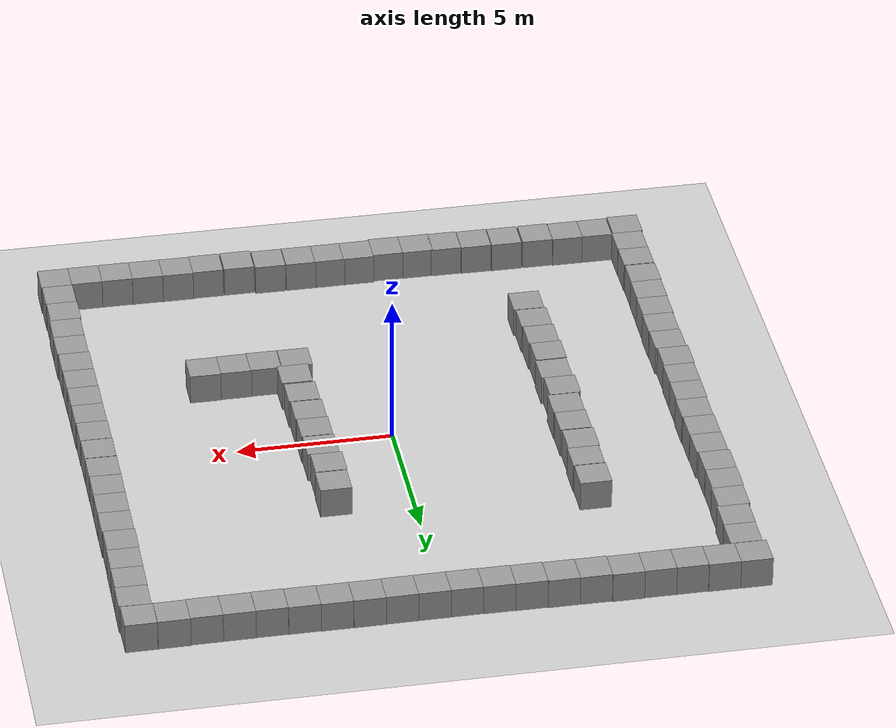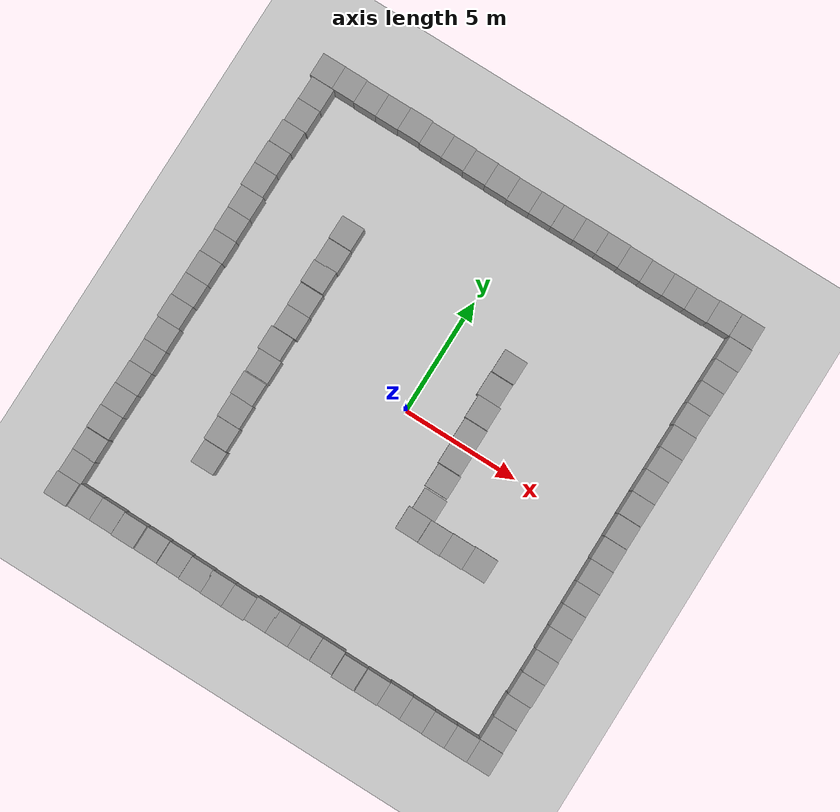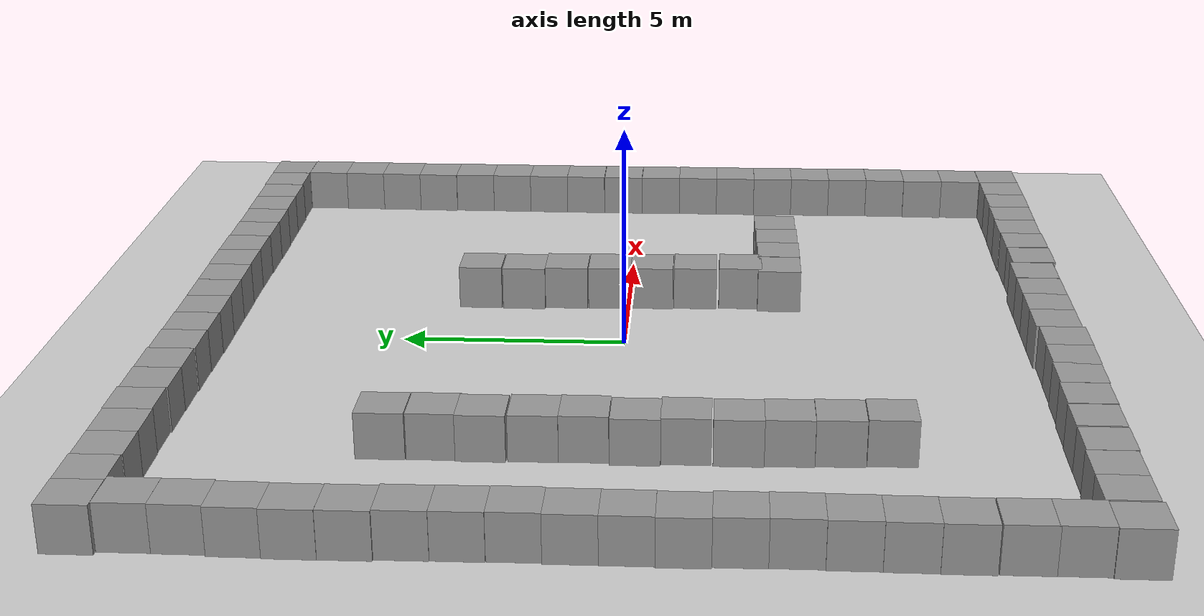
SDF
<sdf version="1.7">
 <world name="default">
  <light name="sun" type="directional">
   <pose>0 0 10 0 -0 0</pose>
   <diffuse>0.8 0.8 0.8 1</diffuse>
   <specular>0.2 0.2 0.2 1</specular>
   <attenuation>
    <range>1000</range>
    <constant>0.9</constant>
    <linear>0.01</linear>
    <quadratic>0.001</quadratic>
   </attenuation>
   <direction>-0.5 0.1 -0.9</direction>
   <spot><inner_angle>0</inner_angle><outer_angle>0</outer_angle><falloff>0</falloff></spot>
  </light>
  <model name="ground_plane">
   <static>1</static>
   <link name="link">
    <collision name="collision">
     <geometry><plane><normal>0 0 1</normal><size>100 100</size></plane></geometry>
     <surface>
      <contact><collide_bitmask>65535</collide_bitmask></contact>
      <friction><ode><mu>100</mu><mu2>50</mu2></ode></friction>
     </surface>
    </collision>
    <visual name="visual">
     <cast_shadows>0</cast_shadows>
     <geometry><plane><normal>0 0 1</normal><size>100 100</size></plane></geometry>
     <material>
      <script><uri>file://media/materials/scripts/gazebo.material</uri><name>Gazebo/Grey</name></script>
     </material>
    </visual>
   </link>
  </model>
  <gravity>0 0 -9.8</gravity>
  <magnetic_field>6e-06 2.3e-05 -4.2e-05</magnetic_field>
  <atmosphere type="adiabatic"/>
  <physics type="ode">
   <max_step_size>0.001</max_step_size>
   <real_time_factor>1</real_time_factor>
   <real_time_update_rate>1000</real_time_update_rate>
  </physics>
  <scene><ambient>0.4 0.4 0.4 1</ambient><background>0.7 0.7 0.7 1</background><shadows>1</shadows></scene>
  <spherical_coordinates>
   <surface_model>EARTH_WGS84</surface_model>
   <latitude_deg>0</latitude_deg>
   <longitude_deg>0</longitude_deg>
   <elevation>0</elevation>
   <heading_deg>0</heading_deg>
  </spherical_coordinates>
  <model name="unit_box">
   <pose>-9.51327 -9.50621 0.5 0 -0 -0.002436</pose>
   <link name="link">
    <inertial>
     <mass>1</mass>
     <inertia>
      <ixx>0.166667</ixx>
      <ixy>0</ixy>
      <ixz>0</ixz>
      <iyy>0.166667</iyy>
      <iyz>0</iyz>
      <izz>0.166667</izz>
     </inertia>
    </inertial>
    <collision name="collision"><geometry><box><size>1 1 1</size></box></geometry></collision>
    <visual name="visual">
     <geometry><box><size>1 1 1</size></box></geometry>
     <material>
      <script><name>Gazebo/Grey</name><uri>file://media/materials/scripts/gazebo.material</uri></script>
     </material>
    </visual>
   </link>
  </model>
  <model name="unit_box_0">
   <pose>-9.47183 -8.5063 0.5 -0 -0 -0.002438</pose>
   <link name="link">
    <inertial>
     <mass>1</mass>
     <inertia>
      <ixx>0.166667</ixx>
      <ixy>0</ixy>
      <ixz>0</ixz>
      <iyy>0.166667</iyy>
      <iyz>0</iyz>
      <izz>0.166667</izz>
     </inertia>
    </inertial>
    <collision name="collision"><geometry><box><size>1 1 1</size></box></geometry></collision>
    <visual name="visual">
     <geometry><box><size>1 1 1</size></box></geometry>
     <material>
      <script><name>Gazebo/Grey</name><uri>file://media/materials/scripts/gazebo.material</uri></script>
     </material>
    </visual>
   </link>
  </model>
  <model name="unit_box_0_clone">
   <pose>-9.47665 -7.53043 0.499995 0 -1e-05 -0.002496</pose>
   <link name="link">
    <inertial>
     <mass>1</mass>
     <inertia>
      <ixx>0.166667</ixx>
      <ixy>0</ixy>
      <ixz>0</ixz>
      <iyy>0.166667</iyy>
      <iyz>0</iyz>
      <izz>0.166667</izz>
     </inertia>
    </inertial>
    <collision name="collision"><geometry><box><size>1 1 1</size></box></geometry></collision>
    <visual name="visual">
     <geometry><box><size>1 1 1</size></box></geometry>
     <material>
      <script><name>Gazebo/Grey</name><uri>file://media/materials/scripts/gazebo.material</uri></script>
     </material>
    </visual>
   </link>
  </model>
  <model name="unit_box_0_clone_0">
   <pose>-9.49208 -6.5062 0.499995 0 -1e-05 -0.0025</pose>
   <link name="link">
    <inertial>
     <mass>1</mass>
     <inertia>
      <ixx>0.166667</ixx>
      <ixy>0</ixy>
      <ixz>0</ixz>
      <iyy>0.166667</iyy>
      <iyz>0</iyz>
      <izz>0.166667</izz>
     </inertia>
    </inertial>
    <collision name="collision"><geometry><box><size>1 1 1</size></box></geometry></collision>
    <visual name="visual">
     <geometry><box><size>1 1 1</size></box></geometry>
     <material>
      <script><name>Gazebo/Grey</name><uri>file://media/materials/scripts/gazebo.material</uri></script>
     </material>
    </visual>
   </link>
  </model>
  <model name="unit_box_0_clone_1">
   <pose>-9.47626 -5.50624 0.499995 0 -1e-05 -0.002502</pose>
   <link name="link">
    <inertial>
     <mass>1</mass>
     <inertia>
      <ixx>0.166667</ixx>
      <ixy>0</ixy>
      <ixz>0</ixz>
      <iyy>0.166667</iyy>
      <iyz>0</iyz>
      <izz>0.166667</izz>
     </inertia>
    </inertial>
    <collision name="collision"><geometry><box><size>1 1 1</size></box></geometry></collision>
    <visual name="visual">
     <geometry><box><size>1 1 1</size></box></geometry>
     <material>
      <script><name>Gazebo/Grey</name><uri>file://media/materials/scripts/gazebo.material</uri></script>
     </material>
    </visual>
   </link>
  </model>
  <model name="unit_box_0_clone_2">
   <pose>-9.4605 -4.50624 0.5 -0 -0 -0.002559</pose>
   <link name="link">
    <inertial>
     <mass>1</mass>
     <inertia>
      <ixx>0.166667</ixx>
      <ixy>0</ixy>
      <ixz>0</ixz>
      <iyy>0.166667</iyy>
      <iyz>0</iyz>
      <izz>0.166667</izz>
     </inertia>
    </inertial>
    <collision name="collision"><geometry><box><size>1 1 1</size></box></geometry></collision>
    <visual name="visual">
     <geometry><box><size>1 1 1</size></box></geometry>
     <material>
      <script><name>Gazebo/Grey</name><uri>file://media/materials/scripts/gazebo.material</uri></script>
     </material>
    </visual>
   </link>
  </model>
  <model name="unit_box_0_clone_3">
   <pose>-9.43668 -3.50629 0.499995 -1e-05 0 -0.002576</pose>
   <link name="link">
    <inertial>
     <mass>1</mass>
     <inertia>
      <ixx>0.166667</ixx>
      <ixy>0</ixy>
      <ixz>0</ixz>
      <iyy>0.166667</iyy>
      <iyz>0</iyz>
      <izz>0.166667</izz>
     </inertia>
    </inertial>
    <collision name="collision"><geometry><box><size>1 1 1</size></box></geometry></collision>
    <visual name="visual">
     <geometry><box><size>1 1 1</size></box></geometry>
     <material>
      <script><name>Gazebo/Grey</name><uri>file://media/materials/scripts/gazebo.material</uri></script>
     </material>
    </visual>
   </link>
  </model>
  <model name="unit_box_0_clone_4">
   <pose>-9.44901 -2.50624 0.5 0 0 -0.002604</pose>
   <link name="link">
    <inertial>
     <mass>1</mass>
     <inertia>
      <ixx>0.166667</ixx>
      <ixy>0</ixy>
      <ixz>0</ixz>
      <iyy>0.166667</iyy>
      <iyz>0</iyz>
      <izz>0.166667</izz>
     </inertia>
    </inertial>
    <collision name="collision"><geometry><box><size>1 1 1</size></box></geometry></collision>
    <visual name="visual">
     <geometry><box><size>1 1 1</size></box></geometry>
     <material>
      <script><name>Gazebo/Grey</name><uri>file://media/materials/scripts/gazebo.material</uri></script>
     </material>
    </visual>
   </link>
  </model>
  <model name="unit_box_0_clone_5">
   <pose>-9.49911 -1.50602 0.5 0 0 -0.002766</pose>
   <link name="link">
    <inertial>
     <mass>1</mass>
     <inertia>
      <ixx>0.166667</ixx>
      <ixy>0</ixy>
      <ixz>0</ixz>
      <iyy>0.166667</iyy>
      <iyz>0</iyz>
      <izz>0.166667</izz>
     </inertia>
    </inertial>
    <collision name="collision"><geometry><box><size>1 1 1</size></box></geometry></collision>
    <visual name="visual">
     <geometry><box><size>1 1 1</size></box></geometry>
     <material>
      <script><name>Gazebo/Grey</name><uri>file://media/materials/scripts/gazebo.material</uri></script>
     </material>
    </visual>
   </link>
  </model>
  <model name="unit_box_0_clone_6">
   <pose>-9.47202 -0.506039 0.5 0 -0 -0.002882</pose>
   <link name="link">
    <inertial>
     <mass>1</mass>
     <inertia>
      <ixx>0.166667</ixx>
      <ixy>0</ixy>
      <ixz>0</ixz>
      <iyy>0.166667</iyy>
      <iyz>0</iyz>
      <izz>0.166667</izz>
     </inertia>
    </inertial>
    <collision name="collision"><geometry><box><size>1 1 1</size></box></geometry></collision>
    <visual name="visual">
     <geometry><box><size>1 1 1</size></box></geometry>
     <material>
      <script><name>Gazebo/Grey</name><uri>file://media/materials/scripts/gazebo.material</uri></script>
     </material>
    </visual>
   </link>
  </model>
  <model name="unit_box_0_clone_7">
   <pose>-9.46766 0.493972 0.499995 0 -1e-05 -0.002908</pose>
   <link name="link">
    <inertial>
     <mass>1</mass>
     <inertia>
      <ixx>0.166667</ixx>
      <ixy>0</ixy>
      <ixz>0</ixz>
      <iyy>0.166667</iyy>
      <iyz>0</iyz>
      <izz>0.166667</izz>
     </inertia>
    </inertial>
    <collision name="collision"><geometry><box><size>1 1 1</size></box></geometry></collision>
    <visual name="visual">
     <geometry><box><size>1 1 1</size></box></geometry>
     <material>
      <script><name>Gazebo/Grey</name><uri>file://media/materials/scripts/gazebo.material</uri></script>
     </material>
    </visual>
   </link>
  </model>
  <model name="unit_box_0_clone_8">
   <pose>-9.43801 1.49392 0.5 0 0 -0.00297</pose>
   <link name="link">
    <inertial>
     <mass>1</mass>
     <inertia>
      <ixx>0.166667</ixx>
      <ixy>0</ixy>
      <ixz>0</ixz>
      <iyy>0.166667</iyy>
      <iyz>0</iyz>
      <izz>0.166667</izz>
     </inertia>
    </inertial>
    <collision name="collision"><geometry><box><size>1 1 1</size></box></geometry></collision>
    <visual name="visual">
     <geometry><box><size>1 1 1</size></box></geometry>
     <material>
      <script><name>Gazebo/Grey</name><uri>file://media/materials/scripts/gazebo.material</uri></script>
     </material>
    </visual>
   </link>
  </model>
  <model name="unit_box_0_clone_9">
   <pose>-9.45504 2.49411 0.499995 -0 -1e-05 -0.003236</pose>
   <link name="link">
    <inertial>
     <mass>1</mass>
     <inertia>
      <ixx>0.166667</ixx>
      <ixy>0</ixy>
      <ixz>0</ixz>
      <iyy>0.166667</iyy>
      <iyz>0</iyz>
      <izz>0.166667</izz>
     </inertia>
    </inertial>
    <collision name="collision"><geometry><box><size>1 1 1</size></box></geometry></collision>
    <visual name="visual">
     <geometry><box><size>1 1 1</size></box></geometry>
     <material>
      <script><name>Gazebo/Grey</name><uri>file://media/materials/scripts/gazebo.material</uri></script>
     </material>
    </visual>
   </link>
  </model>
  <model name="unit_box_0_clone_10">
   <pose>-9.46283 3.49415 0.5 -0 -0 -0.003247</pose>
   <link name="link">
    <inertial>
     <mass>1</mass>
     <inertia>
      <ixx>0.166667</ixx>
      <ixy>0</ixy>
      <ixz>0</ixz>
      <iyy>0.166667</iyy>
      <iyz>0</iyz>
      <izz>0.166667</izz>
     </inertia>
    </inertial>
    <collision name="collision"><geometry><box><size>1 1 1</size></box></geometry></collision>
    <visual name="visual">
     <geometry><box><size>1 1 1</size></box></geometry>
     <material>
      <script><name>Gazebo/Grey</name><uri>file://media/materials/scripts/gazebo.material</uri></script>
     </material>
    </visual>
   </link>
  </model>
  <model name="unit_box_0_clone_11">
   <pose>-9.50926 4.49438 0.5 -0 -0 -0.003385</pose>
   <link name="link">
    <inertial>
     <mass>1</mass>
     <inertia>
      <ixx>0.166667</ixx>
      <ixy>0</ixy>
      <ixz>0</ixz>
      <iyy>0.166667</iyy>
      <iyz>0</iyz>
      <izz>0.166667</izz>
     </inertia>
    </inertial>
    <collision name="collision"><geometry><box><size>1 1 1</size></box></geometry></collision>
    <visual name="visual">
     <geometry><box><size>1 1 1</size></box></geometry>
     <material>
      <script><name>Gazebo/Grey</name><uri>file://media/materials/scripts/gazebo.material</uri></script>
     </material>
    </visual>
   </link>
  </model>
  <model name="unit_box_0_clone_12">
   <pose>-9.51318 5.49463 0.499995 -1e-05 -0 -0.003831</pose>
   <link name="link">
    <inertial>
     <mass>1</mass>
     <inertia>
      <ixx>0.166667</ixx>
      <ixy>0</ixy>
      <ixz>0</ixz>
      <iyy>0.166667</iyy>
      <iyz>0</iyz>
      <izz>0.166667</izz>
     </inertia>
    </inertial>
    <collision name="collision"><geometry><box><size>1 1 1</size></box></geometry></collision>
    <visual name="visual">
     <geometry><box><size>1 1 1</size></box></geometry>
     <material>
      <script><name>Gazebo/Grey</name><uri>file://media/materials/scripts/gazebo.material</uri></script>
     </material>
    </visual>
   </link>
  </model>
  <model name="unit_box_0_clone_13">
   <pose>-9.48454 6.49519 0.499995 1e-05 0 -0.00525</pose>
   <link name="link">
    <inertial>
     <mass>1</mass>
     <inertia>
      <ixx>0.166667</ixx>
      <ixy>0</ixy>
      <ixz>0</ixz>
      <iyy>0.166667</iyy>
      <iyz>0</iyz>
      <izz>0.166667</izz>
     </inertia>
    </inertial>
    <collision name="collision"><geometry><box><size>1 1 1</size></box></geometry></collision>
    <visual name="visual">
     <geometry><box><size>1 1 1</size></box></geometry>
     <material>
      <script><name>Gazebo/Grey</name><uri>file://media/materials/scripts/gazebo.material</uri></script>
     </material>
    </visual>
   </link>
  </model>
  <model name="unit_box_0_clone_14">
   <pose>-9.43049 7.49494 0.499995 -1e-05 -0 -0.005252</pose>
   <link name="link">
    <inertial>
     <mass>1</mass>
     <inertia>
      <ixx>0.166667</ixx>
      <ixy>0</ixy>
      <ixz>0</ixz>
      <iyy>0.166667</iyy>
      <iyz>0</iyz>
      <izz>0.166667</izz>
     </inertia>
    </inertial>
    <collision name="collision"><geometry><box><size>1 1 1</size></box></geometry></collision>
    <visual name="visual">
     <geometry><box><size>1 1 1</size></box></geometry>
     <material>
      <script><name>Gazebo/Grey</name><uri>file://media/materials/scripts/gazebo.material</uri></script>
     </material>
    </visual>
   </link>
  </model>
  <model name="unit_box_0_clone_15">
   <pose>-9.41461 8.49554 0.499995 0 1e-05 -0.00416</pose>
   <link name="link">
    <inertial>
     <mass>1</mass>
     <inertia>
      <ixx>0.166667</ixx>
      <ixy>0</ixy>
      <ixz>0</ixz>
      <iyy>0.166667</iyy>
      <iyz>0</iyz>
      <izz>0.166667</izz>
     </inertia>
    </inertial>
    <collision name="collision"><geometry><box><size>1 1 1</size></box></geometry></collision>
    <visual name="visual">
     <geometry><box><size>1 1 1</size></box></geometry>
     <material>
      <script><name>Gazebo/Grey</name><uri>file://media/materials/scripts/gazebo.material</uri></script>
     </material>
    </visual>
   </link>
  </model>
  <model name="unit_box_0_clone_16">
   <pose>-9.52608 9.50394 0.5 0 -0 0.001646</pose>
   <link name="link">
    <inertial>
     <mass>1</mass>
     <inertia>
      <ixx>0.166667</ixx>
      <ixy>0</ixy>
      <ixz>0</ixz>
      <iyy>0.166667</iyy>
      <iyz>0</iyz>
      <izz>0.166667</izz>
     </inertia>
    </inertial>
    <collision name="collision"><geometry><box><size>1 1 1</size></box></geometry></collision>
    <visual name="visual">
     <geometry><box><size>1 1 1</size></box></geometry>
     <material>
      <script><name>Gazebo/Grey</name><uri>file://media/materials/scripts/gazebo.material</uri></script>
     </material>
    </visual>
   </link>
  </model>
  <model name="unit_box_0_clone_17">
   <pose>-8.52607 9.49983 0.499995 -1e-05 -0 0.001645</pose>
   <link name="link">
    <inertial>
     <mass>1</mass>
     <inertia>
      <ixx>0.166667</ixx>
      <ixy>0</ixy>
      <ixz>0</ixz>
      <iyy>0.166667</iyy>
      <iyz>0</iyz>
      <izz>0.166667</izz>
     </inertia>
    </inertial>
    <collision name="collision"><geometry><box><size>1 1 1</size></box></geometry></collision>
    <visual name="visual">
     <geometry><box><size>1 1 1</size></box></geometry>
     <material>
      <script><name>Gazebo/Grey</name><uri>file://media/materials/scripts/gazebo.material</uri></script>
     </material>
    </visual>
   </link>
  </model>
  <model name="unit_box_0_clone_18">
   <pose>-7.52602 9.48062 0.499995 0 1e-05 0.001646</pose>
   <link name="link">
    <inertial>
     <mass>1</mass>
     <inertia>
      <ixx>0.166667</ixx>
      <ixy>0</ixy>
      <ixz>0</ixz>
      <iyy>0.166667</iyy>
      <iyz>0</iyz>
      <izz>0.166667</izz>
     </inertia>
    </inertial>
    <collision name="collision"><geometry><box><size>1 1 1</size></box></geometry></collision>
    <visual name="visual">
     <geometry><box><size>1 1 1</size></box></geometry>
     <material>
      <script><name>Gazebo/Grey</name><uri>file://media/materials/scripts/gazebo.material</uri></script>
     </material>
    </visual>
   </link>
  </model>
  <model name="unit_box_0_clone_19">
   <pose>-6.52602 9.48045 0.499995 0 -1e-05 0.001652</pose>
   <link name="link">
    <inertial>
     <mass>1</mass>
     <inertia>
      <ixx>0.166667</ixx>
      <ixy>0</ixy>
      <ixz>0</ixz>
      <iyy>0.166667</iyy>
      <iyz>0</iyz>
      <izz>0.166667</izz>
     </inertia>
    </inertial>
    <collision name="collision"><geometry><box><size>1 1 1</size></box></geometry></collision>
    <visual name="visual">
     <geometry><box><size>1 1 1</size></box></geometry>
     <material>
      <script><name>Gazebo/Grey</name><uri>file://media/materials/scripts/gazebo.material</uri></script>
     </material>
    </visual>
   </link>
  </model>
  <model name="unit_box_0_clone_20">
   <pose>-5.52554 9.49635 0.499995 -1e-05 0 0.002675</pose>
   <link name="link">
    <inertial>
     <mass>1</mass>
     <inertia>
      <ixx>0.166667</ixx>
      <ixy>0</ixy>
      <ixz>0</ixz>
      <iyy>0.166667</iyy>
      <iyz>0</iyz>
      <izz>0.166667</izz>
     </inertia>
    </inertial>
    <collision name="collision"><geometry><box><size>1 1 1</size></box></geometry></collision>
    <visual name="visual">
     <geometry><box><size>1 1 1</size></box></geometry>
     <material>
      <script><name>Gazebo/Grey</name><uri>file://media/materials/scripts/gazebo.material</uri></script>
     </material>
    </visual>
   </link>
  </model>
  <model name="unit_box_0_clone_21">
   <pose>-4.52546 9.46827 0.499995 -1e-05 0 0.002676</pose>
   <link name="link">
    <inertial>
     <mass>1</mass>
     <inertia>
      <ixx>0.166667</ixx>
      <ixy>0</ixy>
      <ixz>0</ixz>
      <iyy>0.166667</iyy>
      <iyz>0</iyz>
      <izz>0.166667</izz>
     </inertia>
    </inertial>
    <collision name="collision"><geometry><box><size>1 1 1</size></box></geometry></collision>
    <visual name="visual">
     <geometry><box><size>1 1 1</size></box></geometry>
     <material>
      <script><name>Gazebo/Grey</name><uri>file://media/materials/scripts/gazebo.material</uri></script>
     </material>
    </visual>
   </link>
  </model>
  <model name="unit_box_0_clone_22">
   <pose>-3.52543 9.46151 0.499995 1e-05 -0 0.002676</pose>
   <link name="link">
    <inertial>
     <mass>1</mass>
     <inertia>
      <ixx>0.166667</ixx>
      <ixy>0</ixy>
      <ixz>0</ixz>
      <iyy>0.166667</iyy>
      <iyz>0</iyz>
      <izz>0.166667</izz>
     </inertia>
    </inertial>
    <collision name="collision"><geometry><box><size>1 1 1</size></box></geometry></collision>
    <visual name="visual">
     <geometry><box><size>1 1 1</size></box></geometry>
     <material>
      <script><name>Gazebo/Grey</name><uri>file://media/materials/scripts/gazebo.material</uri></script>
     </material>
    </visual>
   </link>
  </model>
  <model name="unit_box_0_clone_23">
   <pose>-2.52516 9.43862 0.499995 0 -9e-06 0.002665</pose>
   <link name="link">
    <inertial>
     <mass>1</mass>
     <inertia>
      <ixx>0.166667</ixx>
      <ixy>0</ixy>
      <ixz>0</ixz>
      <iyy>0.166667</iyy>
      <iyz>0</iyz>
      <izz>0.166667</izz>
     </inertia>
    </inertial>
    <collision name="collision"><geometry><box><size>1 1 1</size></box></geometry></collision>
    <visual name="visual">
     <geometry><box><size>1 1 1</size></box></geometry>
     <material>
      <script><name>Gazebo/Grey</name><uri>file://media/materials/scripts/gazebo.material</uri></script>
     </material>
    </visual>
   </link>
  </model>
  <model name="unit_box_0_clone_24">
   <pose>-1.52511 9.42517 0.499995 0 9e-06 0.002665</pose>
   <link name="link">
    <inertial>
     <mass>1</mass>
     <inertia>
      <ixx>0.166667</ixx>
      <ixy>0</ixy>
      <ixz>0</ixz>
      <iyy>0.166667</iyy>
      <iyz>0</iyz>
      <izz>0.166667</izz>
     </inertia>
    </inertial>
    <collision name="collision"><geometry><box><size>1 1 1</size></box></geometry></collision>
    <visual name="visual">
     <geometry><box><size>1 1 1</size></box></geometry>
     <material>
      <script><name>Gazebo/Grey</name><uri>file://media/materials/scripts/gazebo.material</uri></script>
     </material>
    </visual>
   </link>
  </model>
  <model name="unit_box_0_clone_25">
   <pose>-0.524617 9.41424 0.499995 1e-05 -0 0.00302</pose>
   <link name="link">
    <inertial>
     <mass>1</mass>
     <inertia>
      <ixx>0.166667</ixx>
      <ixy>0</ixy>
      <ixz>0</ixz>
      <iyy>0.166667</iyy>
      <iyz>0</iyz>
      <izz>0.166667</izz>
     </inertia>
    </inertial>
    <collision name="collision"><geometry><box><size>1 1 1</size></box></geometry></collision>
    <visual name="visual">
     <geometry><box><size>1 1 1</size></box></geometry>
     <material>
      <script><name>Gazebo/Grey</name><uri>file://media/materials/scripts/gazebo.material</uri></script>
     </material>
    </visual>
   </link>
  </model>
  <model name="unit_box_0_clone_26">
   <pose>0.475413 9.42201 0.499995 -0 1e-05 0.002989</pose>
   <link name="link">
    <inertial>
     <mass>1</mass>
     <inertia>
      <ixx>0.166667</ixx>
      <ixy>0</ixy>
      <ixz>0</ixz>
      <iyy>0.166667</iyy>
      <iyz>0</iyz>
      <izz>0.166667</izz>
     </inertia>
    </inertial>
    <collision name="collision"><geometry><box><size>1 1 1</size></box></geometry></collision>
    <visual name="visual">
     <geometry><box><size>1 1 1</size></box></geometry>
     <material>
      <script><name>Gazebo/Grey</name><uri>file://media/materials/scripts/gazebo.material</uri></script>
     </material>
    </visual>
   </link>
  </model>
  <model name="unit_box_0_clone_27">
   <pose>1.47598 9.4266 0.499995 0 -1e-05 0.004126</pose>
   <link name="link">
    <inertial>
     <mass>1</mass>
     <inertia>
      <ixx>0.166667</ixx>
      <ixy>0</ixy>
      <ixz>0</ixz>
      <iyy>0.166667</iyy>
      <iyz>0</iyz>
      <izz>0.166667</izz>
     </inertia>
    </inertial>
    <collision name="collision"><geometry><box><size>1 1 1</size></box></geometry></collision>
    <visual name="visual">
     <geometry><box><size>1 1 1</size></box></geometry>
     <material>
      <script><name>Gazebo/Grey</name><uri>file://media/materials/scripts/gazebo.material</uri></script>
     </material>
    </visual>
   </link>
  </model>
  <model name="unit_box_0_clone_28">
   <pose>2.47603 9.43966 0.499995 1e-05 -0 0.004095</pose>
   <link name="link">
    <inertial>
     <mass>1</mass>
     <inertia>
      <ixx>0.166667</ixx>
      <ixy>0</ixy>
      <ixz>0</ixz>
      <iyy>0.166667</iyy>
      <iyz>0</iyz>
      <izz>0.166667</izz>
     </inertia>
    </inertial>
    <collision name="collision"><geometry><box><size>1 1 1</size></box></geometry></collision>
    <visual name="visual">
     <geometry><box><size>1 1 1</size></box></geometry>
     <material>
      <script><name>Gazebo/Grey</name><uri>file://media/materials/scripts/gazebo.material</uri></script>
     </material>
    </visual>
   </link>
  </model>
  <model name="unit_box_0_clone_29">
   <pose>3.47703 9.43838 0.499995 1e-05 -0 0.004924</pose>
   <link name="link">
    <inertial>
     <mass>1</mass>
     <inertia>
      <ixx>0.166667</ixx>
      <ixy>0</ixy>
      <ixz>0</ixz>
      <iyy>0.166667</iyy>
      <iyz>0</iyz>
      <izz>0.166667</izz>
     </inertia>
    </inertial>
    <collision name="collision"><geometry><box><size>1 1 1</size></box></geometry></collision>
    <visual name="visual">
     <geometry><box><size>1 1 1</size></box></geometry>
     <material>
      <script><name>Gazebo/Grey</name><uri>file://media/materials/scripts/gazebo.material</uri></script>
     </material>
    </visual>
   </link>
  </model>
  <model name="unit_box_0_clone_30">
   <pose>4.47714 9.42629 0.5 0 -0 0.004955</pose>
   <link name="link">
    <inertial>
     <mass>1</mass>
     <inertia>
      <ixx>0.166667</ixx>
      <ixy>0</ixy>
      <ixz>0</ixz>
      <iyy>0.166667</iyy>
      <iyz>0</iyz>
      <izz>0.166667</izz>
     </inertia>
    </inertial>
    <collision name="collision"><geometry><box><size>1 1 1</size></box></geometry></collision>
    <visual name="visual">
     <geometry><box><size>1 1 1</size></box></geometry>
     <material>
      <script><name>Gazebo/Grey</name><uri>file://media/materials/scripts/gazebo.material</uri></script>
     </material>
    </visual>
   </link>
  </model>
  <model name="unit_box_0_clone_31">
   <pose>5.47732 9.41948 0.499995 1e-05 -0 0.004984</pose>
   <link name="link">
    <inertial>
     <mass>1</mass>
     <inertia>
      <ixx>0.166667</ixx>
      <ixy>0</ixy>
      <ixz>0</ixz>
      <iyy>0.166667</iyy>
      <iyz>0</iyz>
      <izz>0.166667</izz>
     </inertia>
    </inertial>
    <collision name="collision"><geometry><box><size>1 1 1</size></box></geometry></collision>
    <visual name="visual">
     <geometry><box><size>1 1 1</size></box></geometry>
     <material>
      <script><name>Gazebo/Grey</name><uri>file://media/materials/scripts/gazebo.material</uri></script>
     </material>
    </visual>
   </link>
  </model>
  <model name="unit_box_0_clone_32">
   <pose>6.47776 9.43419 0.499995 0 1e-05 0.005791</pose>
   <link name="link">
    <inertial>
     <mass>1</mass>
     <inertia>
      <ixx>0.166667</ixx>
      <ixy>0</ixy>
      <ixz>0</ixz>
      <iyy>0.166667</iyy>
      <iyz>0</iyz>
      <izz>0.166667</izz>
     </inertia>
    </inertial>
    <collision name="collision"><geometry><box><size>1 1 1</size></box></geometry></collision>
    <visual name="visual">
     <geometry><box><size>1 1 1</size></box></geometry>
     <material>
      <script><name>Gazebo/Grey</name><uri>file://media/materials/scripts/gazebo.material</uri></script>
     </material>
    </visual>
   </link>
  </model>
  <model name="unit_box_0_clone_33">
   <pose>7.47774 9.44019 0.499995 0 -1e-05 0.005795</pose>
   <link name="link">
    <inertial>
     <mass>1</mass>
     <inertia>
      <ixx>0.166667</ixx>
      <ixy>0</ixy>
      <ixz>0</ixz>
      <iyy>0.166667</iyy>
      <iyz>0</iyz>
      <izz>0.166667</izz>
     </inertia>
    </inertial>
    <collision name="collision"><geometry><box><size>1 1 1</size></box></geometry></collision>
    <visual name="visual">
     <geometry><box><size>1 1 1</size></box></geometry>
     <material>
      <script><name>Gazebo/Grey</name><uri>file://media/materials/scripts/gazebo.material</uri></script>
     </material>
    </visual>
   </link>
  </model>
  <model name="unit_box_0_clone_34">
   <pose>8.47789 9.46771 0.499995 0 1e-05 0.006374</pose>
   <link name="link">
    <inertial>
     <mass>1</mass>
     <inertia>
      <ixx>0.166667</ixx>
      <ixy>0</ixy>
      <ixz>0</ixz>
      <iyy>0.166667</iyy>
      <iyz>0</iyz>
      <izz>0.166667</izz>
     </inertia>
    </inertial>
    <collision name="collision"><geometry><box><size>1 1 1</size></box></geometry></collision>
    <visual name="visual">
     <geometry><box><size>1 1 1</size></box></geometry>
     <material>
      <script><name>Gazebo/Grey</name><uri>file://media/materials/scripts/gazebo.material</uri></script>
     </material>
    </visual>
   </link>
  </model>
  <model name="unit_box_0_clone_35">
   <pose>9.48043 9.47726 0.499995 -1e-05 -0 0.001214</pose>
   <link name="link">
    <inertial>
     <mass>1</mass>
     <inertia>
      <ixx>0.166667</ixx>
      <ixy>0</ixy>
      <ixz>0</ixz>
      <iyy>0.166667</iyy>
      <iyz>0</iyz>
      <izz>0.166667</izz>
     </inertia>
    </inertial>
    <collision name="collision"><geometry><box><size>1 1 1</size></box></geometry></collision>
    <visual name="visual">
     <geometry><box><size>1 1 1</size></box></geometry>
     <material>
      <script><name>Gazebo/Grey</name><uri>file://media/materials/scripts/gazebo.material</uri></script>
     </material>
    </visual>
   </link>
  </model>
  <model name="unit_box_0_clone_36">
   <pose>9.51247 8.47112 0.499995 -1e-05 0 -0.011233</pose>
   <link name="link">
    <inertial>
     <mass>1</mass>
     <inertia>
      <ixx>0.166667</ixx>
      <ixy>0</ixy>
      <ixz>0</ixz>
      <iyy>0.166667</iyy>
      <iyz>0</iyz>
      <izz>0.166667</izz>
     </inertia>
    </inertial>
    <collision name="collision"><geometry><box><size>1 1 1</size></box></geometry></collision>
    <visual name="visual">
     <geometry><box><size>1 1 1</size></box></geometry>
     <material>
      <script><name>Gazebo/Grey</name><uri>file://media/materials/scripts/gazebo.material</uri></script>
     </material>
    </visual>
   </link>
  </model>
  <model name="unit_box_0_clone_37">
   <pose>9.49321 7.47124 0.5 0 0 -0.011209</pose>
   <link name="link">
    <inertial>
     <mass>1</mass>
     <inertia>
      <ixx>0.166667</ixx>
      <ixy>0</ixy>
      <ixz>0</ixz>
      <iyy>0.166667</iyy>
      <iyz>0</iyz>
      <izz>0.166667</izz>
     </inertia>
    </inertial>
    <collision name="collision"><geometry><box><size>1 1 1</size></box></geometry></collision>
    <visual name="visual">
     <geometry><box><size>1 1 1</size></box></geometry>
     <material>
      <script><name>Gazebo/Grey</name><uri>file://media/materials/scripts/gazebo.material</uri></script>
     </material>
    </visual>
   </link>
  </model>
  <model name="unit_box_0_clone_38">
   <pose>9.47848 6.47134 0.499995 0 -1e-05 -0.011205</pose>
   <link name="link">
    <inertial>
     <mass>1</mass>
     <inertia>
      <ixx>0.166667</ixx>
      <ixy>0</ixy>
      <ixz>0</ixz>
      <iyy>0.166667</iyy>
      <iyz>0</iyz>
      <izz>0.166667</izz>
     </inertia>
    </inertial>
    <collision name="collision"><geometry><box><size>1 1 1</size></box></geometry></collision>
    <visual name="visual">
     <geometry><box><size>1 1 1</size></box></geometry>
     <material>
      <script><name>Gazebo/Grey</name><uri>file://media/materials/scripts/gazebo.material</uri></script>
     </material>
    </visual>
   </link>
  </model>
  <model name="unit_box_0_clone_39">
   <pose>9.45638 5.47152 0.499995 0 1e-05 -0.011199</pose>
   <link name="link">
    <inertial>
     <mass>1</mass>
     <inertia>
      <ixx>0.166667</ixx>
      <ixy>0</ixy>
      <ixz>0</ixz>
      <iyy>0.166667</iyy>
      <iyz>0</iyz>
      <izz>0.166667</izz>
     </inertia>
    </inertial>
    <collision name="collision"><geometry><box><size>1 1 1</size></box></geometry></collision>
    <visual name="visual">
     <geometry><box><size>1 1 1</size></box></geometry>
     <material>
      <script><name>Gazebo/Grey</name><uri>file://media/materials/scripts/gazebo.material</uri></script>
     </material>
    </visual>
   </link>
  </model>
  <model name="unit_box_0_clone_40">
   <pose>9.47455 4.47123 0.5 0 0 -0.011165</pose>
   <link name="link">
    <inertial>
     <mass>1</mass>
     <inertia>
      <ixx>0.166667</ixx>
      <ixy>0</ixy>
      <ixz>0</ixz>
      <iyy>0.166667</iyy>
      <iyz>0</iyz>
      <izz>0.166667</izz>
     </inertia>
    </inertial>
    <collision name="collision"><geometry><box><size>1 1 1</size></box></geometry></collision>
    <visual name="visual">
     <geometry><box><size>1 1 1</size></box></geometry>
     <material>
      <script><name>Gazebo/Grey</name><uri>file://media/materials/scripts/gazebo.material</uri></script>
     </material>
    </visual>
   </link>
  </model>
  <model name="unit_box_0_clone_41">
   <pose>9.46916 3.47119 0.499995 0 1e-05 -0.011081</pose>
   <link name="link">
    <inertial>
     <mass>1</mass>
     <inertia>
      <ixx>0.166667</ixx>
      <ixy>0</ixy>
      <ixz>0</ixz>
      <iyy>0.166667</iyy>
      <iyz>0</iyz>
      <izz>0.166667</izz>
     </inertia>
    </inertial>
    <collision name="collision"><geometry><box><size>1 1 1</size></box></geometry></collision>
    <visual name="visual">
     <geometry><box><size>1 1 1</size></box></geometry>
     <material>
      <script><name>Gazebo/Grey</name><uri>file://media/materials/scripts/gazebo.material</uri></script>
     </material>
    </visual>
   </link>
  </model>
  <model name="unit_box_0_clone_42">
   <pose>9.45905 2.47123 0.499995 0 -1e-05 -0.011057</pose>
   <link name="link">
    <inertial>
     <mass>1</mass>
     <inertia>
      <ixx>0.166667</ixx>
      <ixy>0</ixy>
      <ixz>0</ixz>
      <iyy>0.166667</iyy>
      <iyz>0</iyz>
      <izz>0.166667</izz>
     </inertia>
    </inertial>
    <collision name="collision"><geometry><box><size>1 1 1</size></box></geometry></collision>
    <visual name="visual">
     <geometry><box><size>1 1 1</size></box></geometry>
     <material>
      <script><name>Gazebo/Grey</name><uri>file://media/materials/scripts/gazebo.material</uri></script>
     </material>
    </visual>
   </link>
  </model>
  <model name="unit_box_0_clone_43">
   <pose>9.45523 1.46932 0.5 0 0 -0.007247</pose>
   <link name="link">
    <inertial>
     <mass>1</mass>
     <inertia>
      <ixx>0.166667</ixx>
      <ixy>0</ixy>
      <ixz>0</ixz>
      <iyy>0.166667</iyy>
      <iyz>0</iyz>
      <izz>0.166667</izz>
     </inertia>
    </inertial>
    <collision name="collision"><geometry><box><size>1 1 1</size></box></geometry></collision>
    <visual name="visual">
     <geometry><box><size>1 1 1</size></box></geometry>
     <material>
      <script><name>Gazebo/Grey</name><uri>file://media/materials/scripts/gazebo.material</uri></script>
     </material>
    </visual>
   </link>
  </model>
  <model name="unit_box_0_clone_44">
   <pose>9.45428 0.455971 0.499995 0 -1e-05 -0.002437</pose>
   <link name="link">
    <inertial>
     <mass>1</mass>
     <inertia>
      <ixx>0.166667</ixx>
      <ixy>0</ixy>
      <ixz>0</ixz>
      <iyy>0.166667</iyy>
      <iyz>0</iyz>
      <izz>0.166667</izz>
     </inertia>
    </inertial>
    <collision name="collision"><geometry><box><size>1 1 1</size></box></geometry></collision>
    <visual name="visual">
     <geometry><box><size>1 1 1</size></box></geometry>
     <material>
      <script><name>Gazebo/Grey</name><uri>file://media/materials/scripts/gazebo.material</uri></script>
     </material>
    </visual>
   </link>
  </model>
  <model name="unit_box_0_clone_45">
   <pose>9.46141 -0.551452 0.499995 0 1e-05 -0.001599</pose>
   <link name="link">
    <inertial>
     <mass>1</mass>
     <inertia>
      <ixx>0.166667</ixx>
      <ixy>0</ixy>
      <ixz>0</ixz>
      <iyy>0.166667</iyy>
      <iyz>0</iyz>
      <izz>0.166667</izz>
     </inertia>
    </inertial>
    <collision name="collision"><geometry><box><size>1 1 1</size></box></geometry></collision>
    <visual name="visual">
     <geometry><box><size>1 1 1</size></box></geometry>
     <material>
      <script><name>Gazebo/Grey</name><uri>file://media/materials/scripts/gazebo.material</uri></script>
     </material>
    </visual>
   </link>
  </model>
  <model name="unit_box_0_clone_46">
   <pose>9.47739 -1.55163 0.5 1e-06 -0 -0.001295</pose>
   <link name="link">
    <inertial>
     <mass>1</mass>
     <inertia>
      <ixx>0.166667</ixx>
      <ixy>0</ixy>
      <ixz>0</ixz>
      <iyy>0.166667</iyy>
      <iyz>0</iyz>
      <izz>0.166667</izz>
     </inertia>
    </inertial>
    <collision name="collision"><geometry><box><size>1 1 1</size></box></geometry></collision>
    <visual name="visual">
     <geometry><box><size>1 1 1</size></box></geometry>
     <material>
      <script><name>Gazebo/Grey</name><uri>file://media/materials/scripts/gazebo.material</uri></script>
     </material>
    </visual>
   </link>
  </model>
  <model name="unit_box_0_clone_47">
   <pose>9.47653 -2.55164 0.5 -1e-06 -0 -0.001294</pose>
   <link name="link">
    <inertial>
     <mass>1</mass>
     <inertia>
      <ixx>0.166667</ixx>
      <ixy>0</ixy>
      <ixz>0</ixz>
      <iyy>0.166667</iyy>
      <iyz>0</iyz>
      <izz>0.166667</izz>
     </inertia>
    </inertial>
    <collision name="collision"><geometry><box><size>1 1 1</size></box></geometry></collision>
    <visual name="visual">
     <geometry><box><size>1 1 1</size></box></geometry>
     <material>
      <script><name>Gazebo/Grey</name><uri>file://media/materials/scripts/gazebo.material</uri></script>
     </material>
    </visual>
   </link>
  </model>
  <model name="unit_box_0_clone_48">
   <pose>9.48417 -3.55209 0.499995 0 -1e-05 -0.001107</pose>
   <link name="link">
    <inertial>
     <mass>1</mass>
     <inertia>
      <ixx>0.166667</ixx>
      <ixy>0</ixy>
      <ixz>0</ixz>
      <iyy>0.166667</iyy>
      <iyz>0</iyz>
      <izz>0.166667</izz>
     </inertia>
    </inertial>
    <collision name="collision"><geometry><box><size>1 1 1</size></box></geometry></collision>
    <visual name="visual">
     <geometry><box><size>1 1 1</size></box></geometry>
     <material>
      <script><name>Gazebo/Grey</name><uri>file://media/materials/scripts/gazebo.material</uri></script>
     </material>
    </visual>
   </link>
  </model>
  <model name="unit_box_0_clone_49">
   <pose>9.49225 -4.55211 0.499995 -0 -1e-05 -0.0011</pose>
   <link name="link">
    <inertial>
     <mass>1</mass>
     <inertia>
      <ixx>0.166667</ixx>
      <ixy>0</ixy>
      <ixz>0</ixz>
      <iyy>0.166667</iyy>
      <iyz>0</iyz>
      <izz>0.166667</izz>
     </inertia>
    </inertial>
    <collision name="collision"><geometry><box><size>1 1 1</size></box></geometry></collision>
    <visual name="visual">
     <geometry><box><size>1 1 1</size></box></geometry>
     <material>
      <script><name>Gazebo/Grey</name><uri>file://media/materials/scripts/gazebo.material</uri></script>
     </material>
    </visual>
   </link>
  </model>
  <model name="unit_box_0_clone_50">
   <pose>9.51872 -5.55255 0.499995 0 1e-05 -0.001275</pose>
   <link name="link">
    <inertial>
     <mass>1</mass>
     <inertia>
      <ixx>0.166667</ixx>
      <ixy>0</ixy>
      <ixz>0</ixz>
      <iyy>0.166667</iyy>
      <iyz>0</iyz>
      <izz>0.166667</izz>
     </inertia>
    </inertial>
    <collision name="collision"><geometry><box><size>1 1 1</size></box></geometry></collision>
    <visual name="visual">
     <geometry><box><size>1 1 1</size></box></geometry>
     <material>
      <script><name>Gazebo/Grey</name><uri>file://media/materials/scripts/gazebo.material</uri></script>
     </material>
    </visual>
   </link>
  </model>
  <model name="unit_box_0_clone_51">
   <pose>9.51322 -6.55333 0.5 0 -0 -0.001544</pose>
   <link name="link">
    <inertial>
     <mass>1</mass>
     <inertia>
      <ixx>0.166667</ixx>
      <ixy>0</ixy>
      <ixz>0</ixz>
      <iyy>0.166667</iyy>
      <iyz>0</iyz>
      <izz>0.166667</izz>
     </inertia>
    </inertial>
    <collision name="collision"><geometry><box><size>1 1 1</size></box></geometry></collision>
    <visual name="visual">
     <geometry><box><size>1 1 1</size></box></geometry>
     <material>
      <script><name>Gazebo/Grey</name><uri>file://media/materials/scripts/gazebo.material</uri></script>
     </material>
    </visual>
   </link>
  </model>
  <model name="unit_box_0_clone_52">
   <pose>9.47953 -7.55339 0.499995 0 -1e-05 -0.001786</pose>
   <link name="link">
    <inertial>
     <mass>1</mass>
     <inertia>
      <ixx>0.166667</ixx>
      <ixy>0</ixy>
      <ixz>0</ixz>
      <iyy>0.166667</iyy>
      <iyz>0</iyz>
      <izz>0.166667</izz>
     </inertia>
    </inertial>
    <collision name="collision"><geometry><box><size>1 1 1</size></box></geometry></collision>
    <visual name="visual">
     <geometry><box><size>1 1 1</size></box></geometry>
     <material>
      <script><name>Gazebo/Grey</name><uri>file://media/materials/scripts/gazebo.material</uri></script>
     </material>
    </visual>
   </link>
  </model>
  <model name="unit_box_0_clone_53">
   <pose>9.49521 -8.55344 0.5 0 0 -0.00182</pose>
   <link name="link">
    <inertial>
     <mass>1</mass>
     <inertia>
      <ixx>0.166667</ixx>
      <ixy>0</ixy>
      <ixz>0</ixz>
      <iyy>0.166667</iyy>
      <iyz>0</iyz>
      <izz>0.166667</izz>
     </inertia>
    </inertial>
    <collision name="collision"><geometry><box><size>1 1 1</size></box></geometry></collision>
    <visual name="visual">
     <geometry><box><size>1 1 1</size></box></geometry>
     <material>
      <script><name>Gazebo/Grey</name><uri>file://media/materials/scripts/gazebo.material</uri></script>
     </material>
    </visual>
   </link>
  </model>
  <model name="unit_box_0_clone_54">
   <pose>9.51539 -9.55784 0.5 -0 -0 -0.001477</pose>
   <link name="link">
    <inertial>
     <mass>1</mass>
     <inertia>
      <ixx>0.166667</ixx>
      <ixy>0</ixy>
      <ixz>0</ixz>
      <iyy>0.166667</iyy>
      <iyz>0</iyz>
      <izz>0.166667</izz>
     </inertia>
    </inertial>
    <collision name="collision"><geometry><box><size>1 1 1</size></box></geometry></collision>
    <visual name="visual">
     <geometry><box><size>1 1 1</size></box></geometry>
     <material>
      <script><name>Gazebo/Grey</name><uri>file://media/materials/scripts/gazebo.material</uri></script>
     </material>
    </visual>
   </link>
  </model>
  <model name="unit_box_0_clone_55">
   <pose>8.51534 -9.5654 0.5 0 0 -0.001417</pose>
   <link name="link">
    <inertial>
     <mass>1</mass>
     <inertia>
      <ixx>0.166667</ixx>
      <ixy>0</ixy>
      <ixz>0</ixz>
      <iyy>0.166667</iyy>
      <iyz>0</iyz>
      <izz>0.166667</izz>
     </inertia>
    </inertial>
    <collision name="collision"><geometry><box><size>1 1 1</size></box></geometry></collision>
    <visual name="visual">
     <geometry><box><size>1 1 1</size></box></geometry>
     <material>
      <script><name>Gazebo/Grey</name><uri>file://media/materials/scripts/gazebo.material</uri></script>
     </material>
    </visual>
   </link>
  </model>
  <model name="unit_box_0_clone_56">
   <pose>7.51533 -9.5691 0.5 -0 -0 -0.00142</pose>
   <link name="link">
    <inertial>
     <mass>1</mass>
     <inertia>
      <ixx>0.166667</ixx>
      <ixy>0</ixy>
      <ixz>0</ixz>
      <iyy>0.166667</iyy>
      <iyz>0</iyz>
      <izz>0.166667</izz>
     </inertia>
    </inertial>
    <collision name="collision"><geometry><box><size>1 1 1</size></box></geometry></collision>
    <visual name="visual">
     <geometry><box><size>1 1 1</size></box></geometry>
     <material>
      <script><name>Gazebo/Grey</name><uri>file://media/materials/scripts/gazebo.material</uri></script>
     </material>
    </visual>
   </link>
  </model>
  <model name="unit_box_0_clone_57">
   <pose>6.51518 -9.55776 0.499995 1e-05 0 -0.001227</pose>
   <link name="link">
    <inertial>
     <mass>1</mass>
     <inertia>
      <ixx>0.166667</ixx>
      <ixy>0</ixy>
      <ixz>0</ixz>
      <iyy>0.166667</iyy>
      <iyz>0</iyz>
      <izz>0.166667</izz>
     </inertia>
    </inertial>
    <collision name="collision"><geometry><box><size>1 1 1</size></box></geometry></collision>
    <visual name="visual">
     <geometry><box><size>1 1 1</size></box></geometry>
     <material>
      <script><name>Gazebo/Grey</name><uri>file://media/materials/scripts/gazebo.material</uri></script>
     </material>
    </visual>
   </link>
  </model>
  <model name="unit_box_0_clone_58">
   <pose>5.51516 -9.54723 0.499995 0 1e-05 -0.001166</pose>
   <link name="link">
    <inertial>
     <mass>1</mass>
     <inertia>
      <ixx>0.166667</ixx>
      <ixy>0</ixy>
      <ixz>0</ixz>
      <iyy>0.166667</iyy>
      <iyz>0</iyz>
      <izz>0.166667</izz>
     </inertia>
    </inertial>
    <collision name="collision"><geometry><box><size>1 1 1</size></box></geometry></collision>
    <visual name="visual">
     <geometry><box><size>1 1 1</size></box></geometry>
     <material>
      <script><name>Gazebo/Grey</name><uri>file://media/materials/scripts/gazebo.material</uri></script>
     </material>
    </visual>
   </link>
  </model>
  <model name="unit_box_0_clone_59">
   <pose>4.51512 -9.56756 0.499995 -1e-05 -0 -0.00117</pose>
   <link name="link">
    <inertial>
     <mass>1</mass>
     <inertia>
      <ixx>0.166667</ixx>
      <ixy>0</ixy>
      <ixz>0</ixz>
      <iyy>0.166667</iyy>
      <iyz>0</iyz>
      <izz>0.166667</izz>
     </inertia>
    </inertial>
    <collision name="collision"><geometry><box><size>1 1 1</size></box></geometry></collision>
    <visual name="visual">
     <geometry><box><size>1 1 1</size></box></geometry>
     <material>
      <script><name>Gazebo/Grey</name><uri>file://media/materials/scripts/gazebo.material</uri></script>
     </material>
    </visual>
   </link>
  </model>
  <model name="unit_box_0_clone_60">
   <pose>3.48139 -9.57489 0.5 0 0 -0.002438</pose>
   <link name="link">
    <inertial>
     <mass>1</mass>
     <inertia>
      <ixx>0.166667</ixx>
      <ixy>0</ixy>
      <ixz>0</ixz>
      <iyy>0.166667</iyy>
      <iyz>0</iyz>
      <izz>0.166667</izz>
     </inertia>
    </inertial>
    <collision name="collision"><geometry><box><size>1 1 1</size></box></geometry></collision>
    <visual name="visual">
     <geometry><box><size>1 1 1</size></box></geometry>
     <material>
      <script><name>Gazebo/Grey</name><uri>file://media/materials/scripts/gazebo.material</uri></script>
     </material>
    </visual>
   </link>
  </model>
  <model name="unit_box_0_clone_61">
   <pose>2.45456 -9.4995 0.5 0 0 -0.002438</pose>
   <link name="link">
    <inertial>
     <mass>1</mass>
     <inertia>
      <ixx>0.166667</ixx>
      <ixy>0</ixy>
      <ixz>0</ixz>
      <iyy>0.166667</iyy>
      <iyz>0</iyz>
      <izz>0.166667</izz>
     </inertia>
    </inertial>
    <collision name="collision"><geometry><box><size>1 1 1</size></box></geometry></collision>
    <visual name="visual">
     <geometry><box><size>1 1 1</size></box></geometry>
     <material>
      <script><name>Gazebo/Grey</name><uri>file://media/materials/scripts/gazebo.material</uri></script>
     </material>
    </visual>
   </link>
  </model>
  <model name="unit_box_0_clone_62">
   <pose>1.44089 -9.49968 0.5 0 0 -0.002438</pose>
   <link name="link">
    <inertial>
     <mass>1</mass>
     <inertia>
      <ixx>0.166667</ixx>
      <ixy>0</ixy>
      <ixz>0</ixz>
      <iyy>0.166667</iyy>
      <iyz>0</iyz>
      <izz>0.166667</izz>
     </inertia>
    </inertial>
    <collision name="collision"><geometry><box><size>1 1 1</size></box></geometry></collision>
    <visual name="visual">
     <geometry><box><size>1 1 1</size></box></geometry>
     <material>
      <script><name>Gazebo/Grey</name><uri>file://media/materials/scripts/gazebo.material</uri></script>
     </material>
    </visual>
   </link>
  </model>
  <model name="unit_box_0_clone_63">
   <pose>0.473666 -9.50091 0.5 0 0 -0.002438</pose>
   <link name="link">
    <inertial>
     <mass>1</mass>
     <inertia>
      <ixx>0.166667</ixx>
      <ixy>0</ixy>
      <ixz>0</ixz>
      <iyy>0.166667</iyy>
      <iyz>0</iyz>
      <izz>0.166667</izz>
     </inertia>
    </inertial>
    <collision name="collision"><geometry><box><size>1 1 1</size></box></geometry></collision>
    <visual name="visual">
     <geometry><box><size>1 1 1</size></box></geometry>
     <material>
      <script><name>Gazebo/Grey</name><uri>file://media/materials/scripts/gazebo.material</uri></script>
     </material>
    </visual>
   </link>
  </model>
  <model name="unit_box_0_clone_64">
   <pose>-0.47754 -9.49986 0.5 0 0 -0.002438</pose>
   <link name="link">
    <inertial>
     <mass>1</mass>
     <inertia>
      <ixx>0.166667</ixx>
      <ixy>0</ixy>
      <ixz>0</ixz>
      <iyy>0.166667</iyy>
      <iyz>0</iyz>
      <izz>0.166667</izz>
     </inertia>
    </inertial>
    <collision name="collision"><geometry><box><size>1 1 1</size></box></geometry></collision>
    <visual name="visual">
     <geometry><box><size>1 1 1</size></box></geometry>
     <material>
      <script><name>Gazebo/Grey</name><uri>file://media/materials/scripts/gazebo.material</uri></script>
     </material>
    </visual>
   </link>
  </model>
  <model name="unit_box_0_clone_65">
   <pose>-1.47741 -9.55915 0.5 0 0 -0.002438</pose>
   <link name="link">
    <inertial>
     <mass>1</mass>
     <inertia>
      <ixx>0.166667</ixx>
      <ixy>0</ixy>
      <ixz>0</ixz>
      <iyy>0.166667</iyy>
      <iyz>0</iyz>
      <izz>0.166667</izz>
     </inertia>
    </inertial>
    <collision name="collision"><geometry><box><size>1 1 1</size></box></geometry></collision>
    <visual name="visual">
     <geometry><box><size>1 1 1</size></box></geometry>
     <material>
      <script><name>Gazebo/Grey</name><uri>file://media/materials/scripts/gazebo.material</uri></script>
     </material>
    </visual>
   </link>
  </model>
  <model name="unit_box_0_clone_66">
   <pose>-2.46537 -9.54892 0.5 0 0 -0.002438</pose>
   <link name="link">
    <inertial>
     <mass>1</mass>
     <inertia>
      <ixx>0.166667</ixx>
      <ixy>0</ixy>
      <ixz>0</ixz>
      <iyy>0.166667</iyy>
      <iyz>0</iyz>
      <izz>0.166667</izz>
     </inertia>
    </inertial>
    <collision name="collision"><geometry><box><size>1 1 1</size></box></geometry></collision>
    <visual name="visual">
     <geometry><box><size>1 1 1</size></box></geometry>
     <material>
      <script><name>Gazebo/Grey</name><uri>file://media/materials/scripts/gazebo.material</uri></script>
     </material>
    </visual>
   </link>
  </model>
  <model name="unit_box_0_clone_67">
   <pose>-3.41063 -9.5298 0.5 0 0 -0.002438</pose>
   <link name="link">
    <inertial>
     <mass>1</mass>
     <inertia>
      <ixx>0.166667</ixx>
      <ixy>0</ixy>
      <ixz>0</ixz>
      <iyy>0.166667</iyy>
      <iyz>0</iyz>
      <izz>0.166667</izz>
     </inertia>
    </inertial>
    <collision name="collision"><geometry><box><size>1 1 1</size></box></geometry></collision>
    <visual name="visual">
     <geometry><box><size>1 1 1</size></box></geometry>
     <material>
      <script><name>Gazebo/Grey</name><uri>file://media/materials/scripts/gazebo.material</uri></script>
     </material>
    </visual>
   </link>
  </model>
  <model name="unit_box_0_clone_68">
   <pose>-4.41567 -9.50305 0.5 0 0 -0.002438</pose>
   <link name="link">
    <inertial>
     <mass>1</mass>
     <inertia>
      <ixx>0.166667</ixx>
      <ixy>0</ixy>
      <ixz>0</ixz>
      <iyy>0.166667</iyy>
      <iyz>0</iyz>
      <izz>0.166667</izz>
     </inertia>
    </inertial>
    <collision name="collision"><geometry><box><size>1 1 1</size></box></geometry></collision>
    <visual name="visual">
     <geometry><box><size>1 1 1</size></box></geometry>
     <material>
      <script><name>Gazebo/Grey</name><uri>file://media/materials/scripts/gazebo.material</uri></script>
     </material>
    </visual>
   </link>
  </model>
  <model name="unit_box_0_clone_69">
   <pose>-5.43577 -9.48739 0.5 0 0 -0.002438</pose>
   <link name="link">
    <inertial>
     <mass>1</mass>
     <inertia>
      <ixx>0.166667</ixx>
      <ixy>0</ixy>
      <ixz>0</ixz>
      <iyy>0.166667</iyy>
      <iyz>0</iyz>
      <izz>0.166667</izz>
     </inertia>
    </inertial>
    <collision name="collision"><geometry><box><size>1 1 1</size></box></geometry></collision>
    <visual name="visual">
     <geometry><box><size>1 1 1</size></box></geometry>
     <material>
      <script><name>Gazebo/Grey</name><uri>file://media/materials/scripts/gazebo.material</uri></script>
     </material>
    </visual>
   </link>
  </model>
  <model name="unit_box_0_clone_70">
   <pose>-6.47899 -9.48804 0.5 0 0 -0.002438</pose>
   <link name="link">
    <inertial>
     <mass>1</mass>
     <inertia>
      <ixx>0.166667</ixx>
      <ixy>0</ixy>
      <ixz>0</ixz>
      <iyy>0.166667</iyy>
      <iyz>0</iyz>
      <izz>0.166667</izz>
     </inertia>
    </inertial>
    <collision name="collision"><geometry><box><size>1 1 1</size></box></geometry></collision>
    <visual name="visual">
     <geometry><box><size>1 1 1</size></box></geometry>
     <material>
      <script><name>Gazebo/Grey</name><uri>file://media/materials/scripts/gazebo.material</uri></script>
     </material>
    </visual>
   </link>
  </model>
  <model name="unit_box_0_clone_71">
   <pose>-7.4821 -9.4612 0.5 0 0 -0.002438</pose>
   <link name="link">
    <inertial>
     <mass>1</mass>
     <inertia>
      <ixx>0.166667</ixx>
      <ixy>0</ixy>
      <ixz>0</ixz>
      <iyy>0.166667</iyy>
      <iyz>0</iyz>
      <izz>0.166667</izz>
     </inertia>
    </inertial>
    <collision name="collision"><geometry><box><size>1 1 1</size></box></geometry></collision>
    <visual name="visual">
     <geometry><box><size>1 1 1</size></box></geometry>
     <material>
      <script><name>Gazebo/Grey</name><uri>file://media/materials/scripts/gazebo.material</uri></script>
     </material>
    </visual>
   </link>
  </model>
  <model name="unit_box_0_clone_72">
   <pose>-8.47114 -9.45857 0.5 0 0 -0.002438</pose>
   <link name="link">
    <inertial>
     <mass>1</mass>
     <inertia>
      <ixx>0.166667</ixx>
      <ixy>0</ixy>
      <ixz>0</ixz>
      <iyy>0.166667</iyy>
      <iyz>0</iyz>
      <izz>0.166667</izz>
     </inertia>
    </inertial>
    <collision name="collision"><geometry><box><size>1 1 1</size></box></geometry></collision>
    <visual name="visual">
     <geometry><box><size>1 1 1</size></box></geometry>
     <material>
      <script><name>Gazebo/Grey</name><uri>file://media/materials/scripts/gazebo.material</uri></script>
     </material>
    </visual>
   </link>
  </model>
  <model name="unit_box_0_clone_73">
   <pose>-5.45749 -4.50791 0.5 0 0 -0.002438</pose>
   <link name="link">
    <inertial>
     <mass>1</mass>
     <inertia>
      <ixx>0.166667</ixx>
      <ixy>0</ixy>
      <ixz>0</ixz>
      <iyy>0.166667</iyy>
      <iyz>0</iyz>
      <izz>0.166667</izz>
     </inertia>
    </inertial>
    <collision name="collision"><geometry><box><size>1 1 1</size></box></geometry></collision>
    <visual name="visual">
     <geometry><box><size>1 1 1</size></box></geometry>
     <material>
      <script><name>Gazebo/Grey</name><uri>file://media/materials/scripts/gazebo.material</uri></script>
     </material>
    </visual>
   </link>
  </model>
  <model name="unit_box_0_clone_74">
   <pose>-5.49155 -3.50345 0.5 0 0 -0.002438</pose>
   <link name="link">
    <inertial>
     <mass>1</mass>
     <inertia>
      <ixx>0.166667</ixx>
      <ixy>0</ixy>
      <ixz>0</ixz>
      <iyy>0.166667</iyy>
      <iyz>0</iyz>
      <izz>0.166667</izz>
     </inertia>
    </inertial>
    <collision name="collision"><geometry><box><size>1 1 1</size></box></geometry></collision>
    <visual name="visual">
     <geometry><box><size>1 1 1</size></box></geometry>
     <material>
      <script><name>Gazebo/Grey</name><uri>file://media/materials/scripts/gazebo.material</uri></script>
     </material>
    </visual>
   </link>
  </model>
  <model name="unit_box_0_clone_75">
   <pose>-5.5319 -2.51285 0.5 0 0 -0.002438</pose>
   <link name="link">
    <inertial>
     <mass>1</mass>
     <inertia>
      <ixx>0.166667</ixx>
      <ixy>0</ixy>
      <ixz>0</ixz>
      <iyy>0.166667</iyy>
      <iyz>0</iyz>
      <izz>0.166667</izz>
     </inertia>
    </inertial>
    <collision name="collision"><geometry><box><size>1 1 1</size></box></geometry></collision>
    <visual name="visual">
     <geometry><box><size>1 1 1</size></box></geometry>
     <material>
      <script><name>Gazebo/Grey</name><uri>file://media/materials/scripts/gazebo.material</uri></script>
     </material>
    </visual>
   </link>
  </model>
  <model name="unit_box_0_clone_76">
   <pose>-5.50179 -1.47884 0.5 0 0 -0.002438</pose>
   <link name="link">
    <inertial>
     <mass>1</mass>
     <inertia>
      <ixx>0.166667</ixx>
      <ixy>0</ixy>
      <ixz>0</ixz>
      <iyy>0.166667</iyy>
      <iyz>0</iyz>
      <izz>0.166667</izz>
     </inertia>
    </inertial>
    <collision name="collision"><geometry><box><size>1 1 1</size></box></geometry></collision>
    <visual name="visual">
     <geometry><box><size>1 1 1</size></box></geometry>
     <material>
      <script><name>Gazebo/Grey</name><uri>file://media/materials/scripts/gazebo.material</uri></script>
     </material>
    </visual>
   </link>
  </model>
  <model name="unit_box_0_clone_77">
   <pose>-5.57696 -0.488735 0.5 0 0 -0.002438</pose>
   <link name="link">
    <inertial>
     <mass>1</mass>
     <inertia>
      <ixx>0.166667</ixx>
      <ixy>0</ixy>
      <ixz>0</ixz>
      <iyy>0.166667</iyy>
      <iyz>0</iyz>
      <izz>0.166667</izz>
     </inertia>
    </inertial>
    <collision name="collision"><geometry><box><size>1 1 1</size></box></geometry></collision>
    <visual name="visual">
     <geometry><box><size>1 1 1</size></box></geometry>
     <material>
      <script><name>Gazebo/Grey</name><uri>file://media/materials/scripts/gazebo.material</uri></script>
     </material>
    </visual>
   </link>
  </model>
  <model name="unit_box_0_clone_78">
   <pose>-5.49507 0.525794 0.5 0 0 -0.002438</pose>
   <link name="link">
    <inertial>
     <mass>1</mass>
     <inertia>
      <ixx>0.166667</ixx>
      <ixy>0</ixy>
      <ixz>0</ixz>
      <iyy>0.166667</iyy>
      <iyz>0</iyz>
      <izz>0.166667</izz>
     </inertia>
    </inertial>
    <collision name="collision"><geometry><box><size>1 1 1</size></box></geometry></collision>
    <visual name="visual">
     <geometry><box><size>1 1 1</size></box></geometry>
     <material>
      <script><name>Gazebo/Grey</name><uri>file://media/materials/scripts/gazebo.material</uri></script>
     </material>
    </visual>
   </link>
  </model>
  <model name="unit_box_0_clone_79">
   <pose>-5.51245 1.51968 0.5 0 0 -0.002438</pose>
   <link name="link">
    <inertial>
     <mass>1</mass>
     <inertia>
      <ixx>0.166667</ixx>
      <ixy>0</ixy>
      <ixz>0</ixz>
      <iyy>0.166667</iyy>
      <iyz>0</iyz>
      <izz>0.166667</izz>
     </inertia>
    </inertial>
    <collision name="collision"><geometry><box><size>1 1 1</size></box></geometry></collision>
    <visual name="visual">
     <geometry><box><size>1 1 1</size></box></geometry>
     <material>
      <script><name>Gazebo/Grey</name><uri>file://media/materials/scripts/gazebo.material</uri></script>
     </material>
    </visual>
   </link>
  </model>
  <model name="unit_box_0_clone_80">
   <pose>-5.55336 2.55154 0.5 0 0 -0.002438</pose>
   <link name="link">
    <inertial>
     <mass>1</mass>
     <inertia>
      <ixx>0.166667</ixx>
      <ixy>0</ixy>
      <ixz>0</ixz>
      <iyy>0.166667</iyy>
      <iyz>0</iyz>
      <izz>0.166667</izz>
     </inertia>
    </inertial>
    <collision name="collision"><geometry><box><size>1 1 1</size></box></geometry></collision>
    <visual name="visual">
     <geometry><box><size>1 1 1</size></box></geometry>
     <material>
      <script><name>Gazebo/Grey</name><uri>file://media/materials/scripts/gazebo.material</uri></script>
     </material>
    </visual>
   </link>
  </model>
  <model name="unit_box_0_clone_81">
   <pose>-5.51749 3.52366 0.5 0 0 -0.002438</pose>
   <link name="link">
    <inertial>
     <mass>1</mass>
     <inertia>
      <ixx>0.166667</ixx>
      <ixy>0</ixy>
      <ixz>0</ixz>
      <iyy>0.166667</iyy>
      <iyz>0</iyz>
      <izz>0.166667</izz>
     </inertia>
    </inertial>
    <collision name="collision"><geometry><box><size>1 1 1</size></box></geometry></collision>
    <visual name="visual">
     <geometry><box><size>1 1 1</size></box></geometry>
     <material>
      <script><name>Gazebo/Grey</name><uri>file://media/materials/scripts/gazebo.material</uri></script>
     </material>
    </visual>
   </link>
  </model>
  <model name="unit_box_0_clone_82">
   <pose>-5.53536 4.54104 0.5 0 0 -0.002438</pose>
   <link name="link">
    <inertial>
     <mass>1</mass>
     <inertia>
      <ixx>0.166667</ixx>
      <ixy>0</ixy>
      <ixz>0</ixz>
      <iyy>0.166667</iyy>
      <iyz>0</iyz>
      <izz>0.166667</izz>
     </inertia>
    </inertial>
    <collision name="collision"><geometry><box><size>1 1 1</size></box></geometry></collision>
    <visual name="visual">
     <geometry><box><size>1 1 1</size></box></geometry>
     <material>
      <script><name>Gazebo/Grey</name><uri>file://media/materials/scripts/gazebo.material</uri></script>
     </material>
    </visual>
   </link>
  </model>
  <model name="unit_box_0_clone_83">
   <pose>2.49524 3.49522 0.5 0 0 -0.002438</pose>
   <link name="link">
    <inertial>
     <mass>1</mass>
     <inertia>
      <ixx>0.166667</ixx>
      <ixy>0</ixy>
      <ixz>0</ixz>
      <iyy>0.166667</iyy>
      <iyz>0</iyz>
      <izz>0.166667</izz>
     </inertia>
    </inertial>
    <collision name="collision"><geometry><box><size>1 1 1</size></box></geometry></collision>
    <visual name="visual">
     <geometry><box><size>1 1 1</size></box></geometry>
     <material>
      <script><name>Gazebo/Grey</name><uri>file://media/materials/scripts/gazebo.material</uri></script>
     </material>
    </visual>
   </link>
  </model>
  <model name="unit_box_0_clone_84">
   <pose>4.5283 -3.52529 0.5 0 0 -0.002438</pose>
   <link name="link">
    <inertial>
     <mass>1</mass>
     <inertia>
      <ixx>0.166667</ixx>
      <ixy>0</ixy>
      <ixz>0</ixz>
      <iyy>0.166667</iyy>
      <iyz>0</iyz>
      <izz>0.166667</izz>
     </inertia>
    </inertial>
    <collision name="collision"><geometry><box><size>1 1 1</size></box></geometry></collision>
    <visual name="visual">
     <geometry><box><size>1 1 1</size></box></geometry>
     <material>
      <script><name>Gazebo/Grey</name><uri>file://media/materials/scripts/gazebo.material</uri></script>
     </material>
    </visual>
   </link>
  </model>
  <model name="unit_box_0_clone_85">
   <pose>3.56514 -3.54008 0.5 0 0 -0.002438</pose>
   <link name="link">
    <inertial>
     <mass>1</mass>
     <inertia>
      <ixx>0.166667</ixx>
      <ixy>0</ixy>
      <ixz>0</ixz>
      <iyy>0.166667</iyy>
      <iyz>0</iyz>
      <izz>0.166667</izz>
     </inertia>
    </inertial>
    <collision name="collision"><geometry><box><size>1 1 1</size></box></geometry></collision>
    <visual name="visual">
     <geometry><box><size>1 1 1</size></box></geometry>
     <material>
      <script><name>Gazebo/Grey</name><uri>file://media/materials/scripts/gazebo.material</uri></script>
     </material>
    </visual>
   </link>
  </model>
  <model name="unit_box_0_clone_86">
   <pose>2.55408 -3.53163 0.5 0 0 -0.002438</pose>
   <link name="link">
    <inertial>
     <mass>1</mass>
     <inertia>
      <ixx>0.166667</ixx>
      <ixy>0</ixy>
      <ixz>0</ixz>
      <iyy>0.166667</iyy>
      <iyz>0</iyz>
      <izz>0.166667</izz>
     </inertia>
    </inertial>
    <collision name="collision"><geometry><box><size>1 1 1</size></box></geometry></collision>
    <visual name="visual">
     <geometry><box><size>1 1 1</size></box></geometry>
     <material>
      <script><name>Gazebo/Grey</name><uri>file://media/materials/scripts/gazebo.material</uri></script>
     </material>
    </visual>
   </link>
  </model>
  <model name="unit_box_0_clone_87">
   <pose>2.69967 -2.62114 0.5 0 0 -0.002438</pose>
   <link name="link">
    <inertial>
     <mass>1</mass>
     <inertia>
      <ixx>0.166667</ixx>
      <ixy>0</ixy>
      <ixz>0</ixz>
      <iyy>0.166667</iyy>
      <iyz>0</iyz>
      <izz>0.166667</izz>
     </inertia>
    </inertial>
    <collision name="collision"><geometry><box><size>1 1 1</size></box></geometry></collision>
    <visual name="visual">
     <geometry><box><size>1 1 1</size></box></geometry>
     <material>
      <script><name>Gazebo/Grey</name><uri>file://media/materials/scripts/gazebo.material</uri></script>
     </material>
    </visual>
   </link>
  </model>
  <model name="unit_box_0_clone_88">
   <pose>2.64761 -1.56263 0.5 0 0 -0.002438</pose>
   <link name="link">
    <inertial>
     <mass>1</mass>
     <inertia>
      <ixx>0.166667</ixx>
      <ixy>0</ixy>
      <ixz>0</ixz>
      <iyy>0.166667</iyy>
      <iyz>0</iyz>
      <izz>0.166667</izz>
     </inertia>
    </inertial>
    <collision name="collision"><geometry><box><size>1 1 1</size></box></geometry></collision>
    <visual name="visual">
     <geometry><box><size>1 1 1</size></box></geometry>
     <material>
      <script><name>Gazebo/Grey</name><uri>file://media/materials/scripts/gazebo.material</uri></script>
     </material>
    </visual>
   </link>
  </model>
  <model name="unit_box_0_clone_89">
   <pose>2.60655 -0.537864 0.5 0 0 -0.002438</pose>
   <link name="link">
    <inertial>
     <mass>1</mass>
     <inertia>
      <ixx>0.166667</ixx>
      <ixy>0</ixy>
      <ixz>0</ixz>
      <iyy>0.166667</iyy>
      <iyz>0</iyz>
      <izz>0.166667</izz>
     </inertia>
    </inertial>
    <collision name="collision"><geometry><box><size>1 1 1</size></box></geometry></collision>
    <visual name="visual">
     <geometry><box><size>1 1 1</size></box></geometry>
     <material>
      <script><name>Gazebo/Grey</name><uri>file://media/materials/scripts/gazebo.material</uri></script>
     </material>
    </visual>
   </link>
  </model>
  <model name="unit_box_0_clone_90">
   <pose>2.57777 0.451347 0.5 0 0 -0.002438</pose>
   <link name="link">
    <inertial>
     <mass>1</mass>
     <inertia>
      <ixx>0.166667</ixx>
      <ixy>0</ixy>
      <ixz>0</ixz>
      <iyy>0.166667</iyy>
      <iyz>0</iyz>
      <izz>0.166667</izz>
     </inertia>
    </inertial>
    <collision name="collision"><geometry><box><size>1 1 1</size></box></geometry></collision>
    <visual name="visual">
     <geometry><box><size>1 1 1</size></box></geometry>
     <material>
      <script><name>Gazebo/Grey</name><uri>file://media/materials/scripts/gazebo.material</uri></script>
     </material>
    </visual>
   </link>
  </model>
  <model name="unit_box_0_clone_91">
   <pose>2.55384 1.4701 0.5 0 0 -0.002438</pose>
   <link name="link">
    <inertial>
     <mass>1</mass>
     <inertia>
      <ixx>0.166667</ixx>
      <ixy>0</ixy>
      <ixz>0</ixz>
      <iyy>0.166667</iyy>
      <iyz>0</iyz>
      <izz>0.166667</izz>
     </inertia>
    </inertial>
    <collision name="collision"><geometry><box><size>1 1 1</size></box></geometry></collision>
    <visual name="visual">
     <geometry><box><size>1 1 1</size></box></geometry>
     <material>
      <script><name>Gazebo/Grey</name><uri>file://media/materials/scripts/gazebo.material</uri></script>
     </material>
    </visual>
   </link>
  </model>
  <model name="unit_box_0_clone_92">
   <pose>2.47335 2.47004 0.5 0 0 -0.002438</pose>
   <link name="link">
    <inertial>
     <mass>1</mass>
     <inertia>
      <ixx>0.166667</ixx>
      <ixy>0</ixy>
      <ixz>0</ixz>
      <iyy>0.166667</iyy>
      <iyz>0</iyz>
      <izz>0.166667</izz>
     </inertia>
    </inertial>
    <collision name="collision"><geometry><box><size>1 1 1</size></box></geometry></collision>
    <visual name="visual">
     <geometry><box><size>1 1 1</size></box></geometry>
     <material>
      <script><name>Gazebo/Grey</name><uri>file://media/materials/scripts/gazebo.material</uri></script>
     </material>
    </visual>
   </link>
  </model>
  <model name="unit_box_0_clone_93">
   <pose>5.52748 -3.50305 0.5 0 0 -0.002438</pose>
   <link name="link">
    <inertial>
     <mass>1</mass>
     <inertia>
      <ixx>0.166667</ixx>
      <ixy>0</ixy>
      <ixz>0</ixz>
      <iyy>0.166667</iyy>
      <iyz>0</iyz>
      <izz>0.166667</izz>
     </inertia>
    </inertial>
    <collision name="collision"><geometry><box><size>1 1 1</size></box></geometry></collision>
    <visual name="visual">
     <geometry><box><size>1 1 1</size></box></geometry>
     <material>
      <script><name>Gazebo/Grey</name><uri>file://media/materials/scripts/gazebo.material</uri></script>
     </material>
    </visual>
   </link>
  </model>
  <model name="unit_box_0_clone_94">
   <pose>-5.39883 -5.52365 0.5 0 0 -0.002438</pose>
   <link name="link">
    <inertial>
     <mass>1</mass>
     <inertia>
      <ixx>0.166667</ixx>
      <ixy>0</ixy>
      <ixz>0</ixz>
      <iyy>0.166667</iyy>
      <iyz>0</iyz>
      <izz>0.166667</izz>
     </inertia>
    </inertial>
    <collision name="collision"><geometry><box><size>1 1 1</size></box></geometry></collision>
    <visual name="visual">
     <geometry><box><size>1 1 1</size></box></geometry>
     <material>
      <script><name>Gazebo/Grey</name><uri>file://media/materials/scripts/gazebo.material</uri></script>
     </material>
    </visual>
   </link>
  </model>
 </world>
</sdf>
